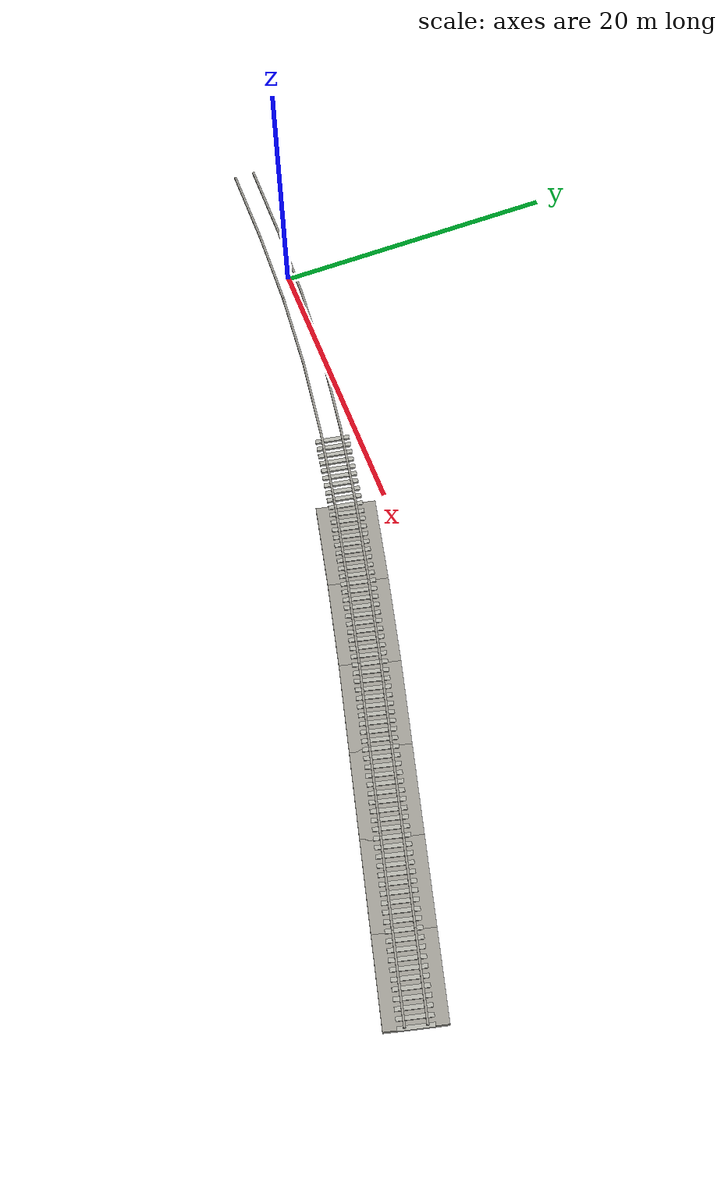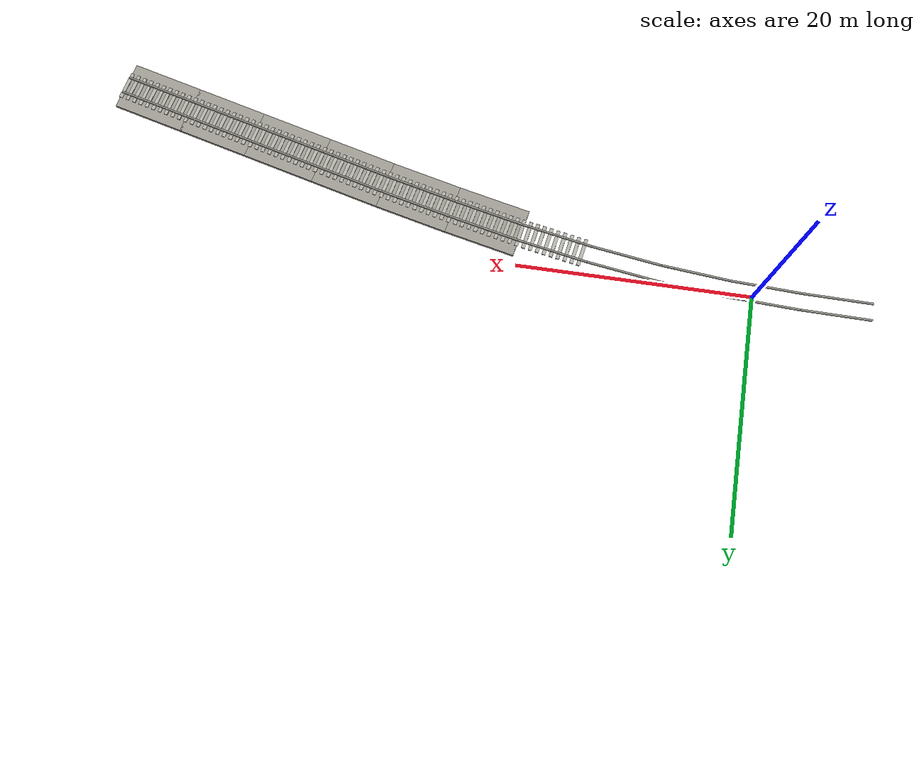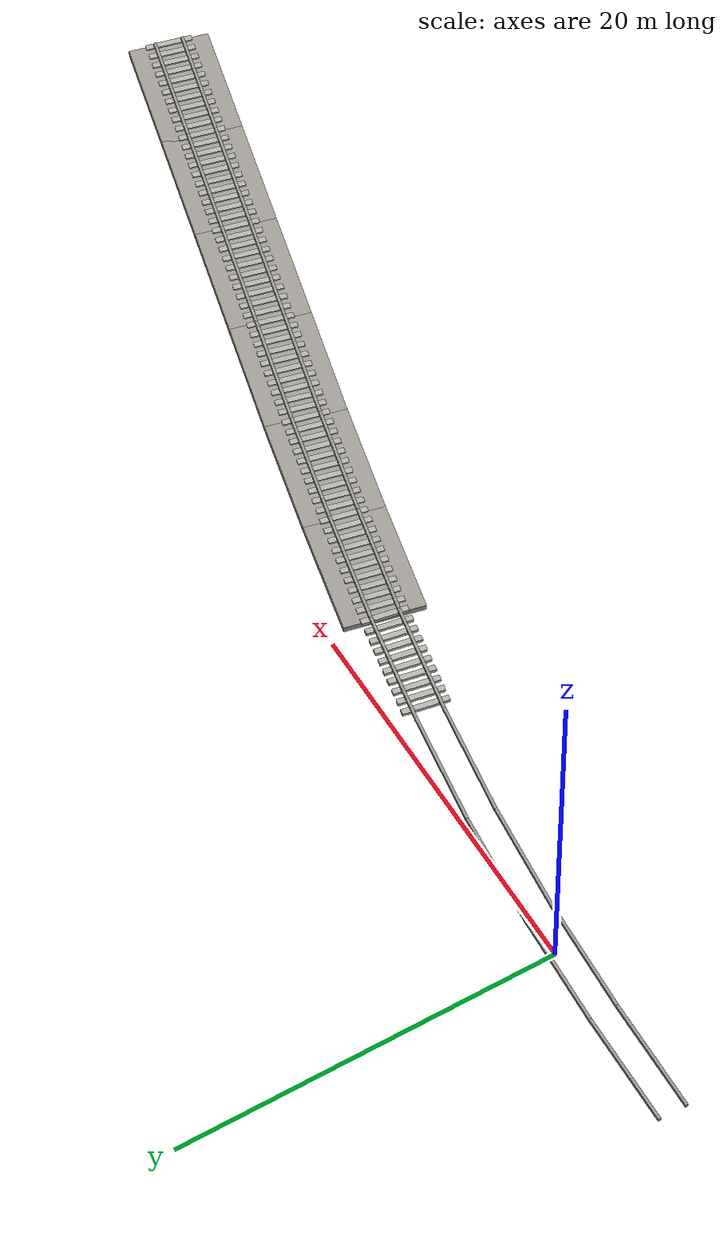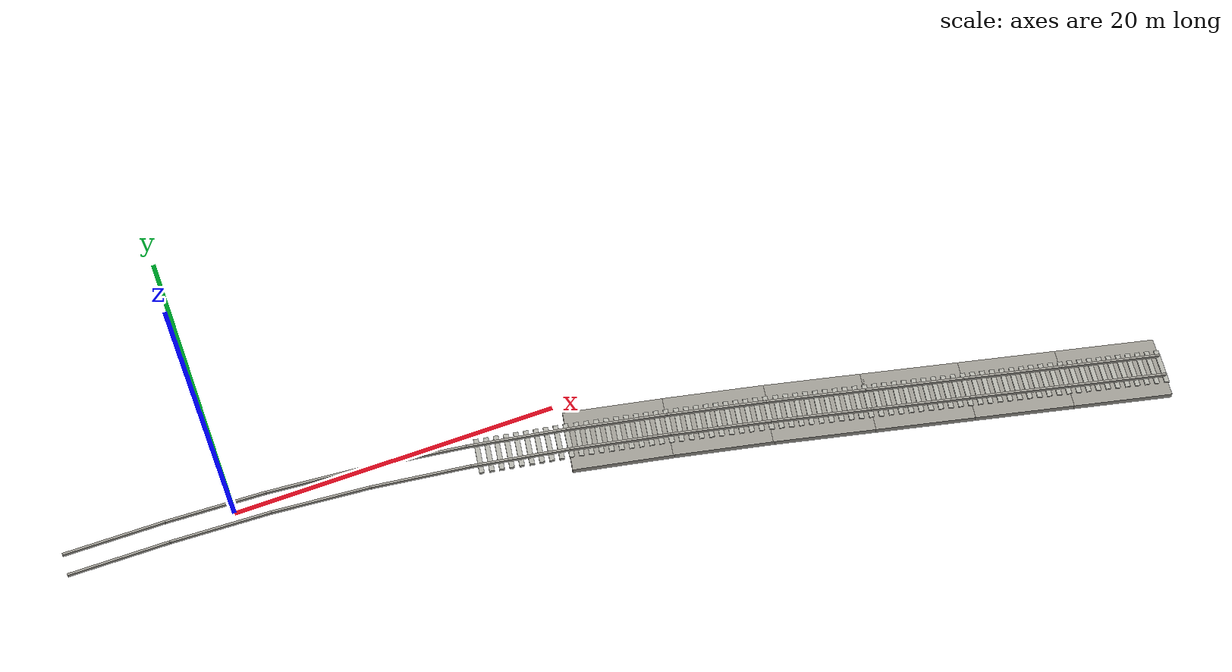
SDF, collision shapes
<?xml version='1.0' encoding='utf-8'?>
<sdf version="1.9">
  <model name="railway_turnout">
    <static>true</static>
    <plugin filename="gz-sim-label-system" name="gz::sim::systems::Label">
      <label>10</label>
    </plugin>
    <link name="turnout_rails_and_ballast">
      <visual name="ballast_transition">
        <geometry>
          <mesh>
            <uri>model://railway_turnout/meshes/ballast_transition.obj</uri>
          </mesh>
        </geometry>
        <material>
          <ambient>0.38 0.38 0.36 1</ambient>
          <diffuse>0.60 0.59 0.56 1</diffuse>
          <pbr>
            <metal>
              <albedo_map>model://track_12m/materials/textures/ballast_albedo.png</albedo_map>
              <roughness>0.98</roughness>
              <metalness>0</metalness>
            </metal>
          </pbr>
        </material>
      </visual>
      <visual name="transition_sleeper_00">
        <pose>-5.700 -0.0390 0.235 0 0 0</pose>
        <geometry>
          <mesh>
            <uri>model://pc_sleeper/meshes/pc_sleeper_concrete.obj</uri>
            <scale>1 1.032465 1</scale>
          </mesh>
        </geometry>
        <material>
          <ambient>0.47 0.47 0.45 1</ambient>
          <diffuse>0.68 0.68 0.65 1</diffuse>
          <pbr>
            <metal>
              <roughness>0.92</roughness>
              <metalness>0</metalness>
            </metal>
          </pbr>
        </material>
      </visual>
      <visual name="transition_sleeper_01">
        <pose>-5.100 -0.0477 0.235 0 0 0</pose>
        <geometry>
          <mesh>
            <uri>model://pc_sleeper/meshes/pc_sleeper_concrete.obj</uri>
            <scale>1 1.039757 1</scale>
          </mesh>
        </geometry>
        <material>
          <ambient>0.47 0.47 0.45 1</ambient>
          <diffuse>0.68 0.68 0.65 1</diffuse>
          <pbr>
            <metal>
              <roughness>0.92</roughness>
              <metalness>0</metalness>
            </metal>
          </pbr>
        </material>
      </visual>
      <visual name="transition_sleeper_02">
        <pose>-4.500 -0.0565 0.235 0 0 0</pose>
        <geometry>
          <mesh>
            <uri>model://pc_sleeper/meshes/pc_sleeper_concrete.obj</uri>
            <scale>1 1.047049 1</scale>
          </mesh>
        </geometry>
        <material>
          <ambient>0.47 0.47 0.45 1</ambient>
          <diffuse>0.68 0.68 0.65 1</diffuse>
          <pbr>
            <metal>
              <roughness>0.92</roughness>
              <metalness>0</metalness>
            </metal>
          </pbr>
        </material>
      </visual>
      <visual name="transition_sleeper_03">
        <pose>-3.900 -0.0652 0.235 0 0 0</pose>
        <geometry>
          <mesh>
            <uri>model://pc_sleeper/meshes/pc_sleeper_concrete.obj</uri>
            <scale>1 1.054340 1</scale>
          </mesh>
        </geometry>
        <material>
          <ambient>0.47 0.47 0.45 1</ambient>
          <diffuse>0.68 0.68 0.65 1</diffuse>
          <pbr>
            <metal>
              <roughness>0.92</roughness>
              <metalness>0</metalness>
            </metal>
          </pbr>
        </material>
      </visual>
      <visual name="transition_sleeper_04">
        <pose>-3.300 -0.0740 0.235 0 0 0</pose>
        <geometry>
          <mesh>
            <uri>model://pc_sleeper/meshes/pc_sleeper_concrete.obj</uri>
            <scale>1 1.061632 1</scale>
          </mesh>
        </geometry>
        <material>
          <ambient>0.47 0.47 0.45 1</ambient>
          <diffuse>0.68 0.68 0.65 1</diffuse>
          <pbr>
            <metal>
              <roughness>0.92</roughness>
              <metalness>0</metalness>
            </metal>
          </pbr>
        </material>
      </visual>
      <visual name="transition_sleeper_05">
        <pose>-2.700 -0.0827 0.235 0 0 0</pose>
        <geometry>
          <mesh>
            <uri>model://pc_sleeper/meshes/pc_sleeper_concrete.obj</uri>
            <scale>1 1.068924 1</scale>
          </mesh>
        </geometry>
        <material>
          <ambient>0.47 0.47 0.45 1</ambient>
          <diffuse>0.68 0.68 0.65 1</diffuse>
          <pbr>
            <metal>
              <roughness>0.92</roughness>
              <metalness>0</metalness>
            </metal>
          </pbr>
        </material>
      </visual>
      <visual name="transition_sleeper_06">
        <pose>-2.100 -0.0915 0.235 0 0 0</pose>
        <geometry>
          <mesh>
            <uri>model://pc_sleeper/meshes/pc_sleeper_concrete.obj</uri>
            <scale>1 1.076215 1</scale>
          </mesh>
        </geometry>
        <material>
          <ambient>0.47 0.47 0.45 1</ambient>
          <diffuse>0.68 0.68 0.65 1</diffuse>
          <pbr>
            <metal>
              <roughness>0.92</roughness>
              <metalness>0</metalness>
            </metal>
          </pbr>
        </material>
      </visual>
      <visual name="transition_sleeper_07">
        <pose>-1.500 -0.1002 0.235 0 0 0</pose>
        <geometry>
          <mesh>
            <uri>model://pc_sleeper/meshes/pc_sleeper_concrete.obj</uri>
            <scale>1 1.083507 1</scale>
          </mesh>
        </geometry>
        <material>
          <ambient>0.47 0.47 0.45 1</ambient>
          <diffuse>0.68 0.68 0.65 1</diffuse>
          <pbr>
            <metal>
              <roughness>0.92</roughness>
              <metalness>0</metalness>
            </metal>
          </pbr>
        </material>
      </visual>
      <visual name="transition_sleeper_08">
        <pose>-0.900 -0.1109 0.235 0 0 0</pose>
        <geometry>
          <mesh>
            <uri>model://pc_sleeper/meshes/pc_sleeper_concrete.obj</uri>
            <scale>1 1.092431 1</scale>
          </mesh>
        </geometry>
        <material>
          <ambient>0.47 0.47 0.45 1</ambient>
          <diffuse>0.68 0.68 0.65 1</diffuse>
          <pbr>
            <metal>
              <roughness>0.92</roughness>
              <metalness>0</metalness>
            </metal>
          </pbr>
        </material>
      </visual>
      <visual name="transition_sleeper_09">
        <pose>-0.300 -0.1314 0.235 0 0 0</pose>
        <geometry>
          <mesh>
            <uri>model://pc_sleeper/meshes/pc_sleeper_concrete.obj</uri>
            <scale>1 1.109514 1</scale>
          </mesh>
        </geometry>
        <material>
          <ambient>0.47 0.47 0.45 1</ambient>
          <diffuse>0.68 0.68 0.65 1</diffuse>
          <pbr>
            <metal>
              <roughness>0.92</roughness>
              <metalness>0</metalness>
            </metal>
          </pbr>
        </material>
      </visual>
      <visual name="transition_sleeper_10">
        <pose>0.300 -0.1519 0.235 0 0 0</pose>
        <geometry>
          <mesh>
            <uri>model://pc_sleeper/meshes/pc_sleeper_concrete.obj</uri>
            <scale>1 1.126597 1</scale>
          </mesh>
        </geometry>
        <material>
          <ambient>0.47 0.47 0.45 1</ambient>
          <diffuse>0.68 0.68 0.65 1</diffuse>
          <pbr>
            <metal>
              <roughness>0.92</roughness>
              <metalness>0</metalness>
            </metal>
          </pbr>
        </material>
      </visual>
      <visual name="transition_sleeper_11">
        <pose>0.900 -0.1724 0.235 0 0 0</pose>
        <geometry>
          <mesh>
            <uri>model://pc_sleeper/meshes/pc_sleeper_concrete.obj</uri>
            <scale>1 1.143681 1</scale>
          </mesh>
        </geometry>
        <material>
          <ambient>0.47 0.47 0.45 1</ambient>
          <diffuse>0.68 0.68 0.65 1</diffuse>
          <pbr>
            <metal>
              <roughness>0.92</roughness>
              <metalness>0</metalness>
            </metal>
          </pbr>
        </material>
      </visual>
      <visual name="transition_sleeper_12">
        <pose>1.500 -0.1929 0.235 0 0 0</pose>
        <geometry>
          <mesh>
            <uri>model://pc_sleeper/meshes/pc_sleeper_concrete.obj</uri>
            <scale>1 1.160764 1</scale>
          </mesh>
        </geometry>
        <material>
          <ambient>0.47 0.47 0.45 1</ambient>
          <diffuse>0.68 0.68 0.65 1</diffuse>
          <pbr>
            <metal>
              <roughness>0.92</roughness>
              <metalness>0</metalness>
            </metal>
          </pbr>
        </material>
      </visual>
      <visual name="transition_sleeper_13">
        <pose>2.100 -0.2134 0.235 0 0 0</pose>
        <geometry>
          <mesh>
            <uri>model://pc_sleeper/meshes/pc_sleeper_concrete.obj</uri>
            <scale>1 1.177847 1</scale>
          </mesh>
        </geometry>
        <material>
          <ambient>0.47 0.47 0.45 1</ambient>
          <diffuse>0.68 0.68 0.65 1</diffuse>
          <pbr>
            <metal>
              <roughness>0.92</roughness>
              <metalness>0</metalness>
            </metal>
          </pbr>
        </material>
      </visual>
      <visual name="transition_sleeper_14">
        <pose>2.700 -0.2339 0.235 0 0 0</pose>
        <geometry>
          <mesh>
            <uri>model://pc_sleeper/meshes/pc_sleeper_concrete.obj</uri>
            <scale>1 1.194931 1</scale>
          </mesh>
        </geometry>
        <material>
          <ambient>0.47 0.47 0.45 1</ambient>
          <diffuse>0.68 0.68 0.65 1</diffuse>
          <pbr>
            <metal>
              <roughness>0.92</roughness>
              <metalness>0</metalness>
            </metal>
          </pbr>
        </material>
      </visual>
      <visual name="transition_sleeper_15">
        <pose>3.300 -0.2544 0.235 0 0 0</pose>
        <geometry>
          <mesh>
            <uri>model://pc_sleeper/meshes/pc_sleeper_concrete.obj</uri>
            <scale>1 1.212014 1</scale>
          </mesh>
        </geometry>
        <material>
          <ambient>0.47 0.47 0.45 1</ambient>
          <diffuse>0.68 0.68 0.65 1</diffuse>
          <pbr>
            <metal>
              <roughness>0.92</roughness>
              <metalness>0</metalness>
            </metal>
          </pbr>
        </material>
      </visual>
      <visual name="transition_sleeper_16">
        <pose>3.900 -0.2749 0.235 0 0 0</pose>
        <geometry>
          <mesh>
            <uri>model://pc_sleeper/meshes/pc_sleeper_concrete.obj</uri>
            <scale>1 1.229097 1</scale>
          </mesh>
        </geometry>
        <material>
          <ambient>0.47 0.47 0.45 1</ambient>
          <diffuse>0.68 0.68 0.65 1</diffuse>
          <pbr>
            <metal>
              <roughness>0.92</roughness>
              <metalness>0</metalness>
            </metal>
          </pbr>
        </material>
      </visual>
      <visual name="transition_sleeper_17">
        <pose>4.500 -0.2954 0.235 0 0 0</pose>
        <geometry>
          <mesh>
            <uri>model://pc_sleeper/meshes/pc_sleeper_concrete.obj</uri>
            <scale>1 1.246181 1</scale>
          </mesh>
        </geometry>
        <material>
          <ambient>0.47 0.47 0.45 1</ambient>
          <diffuse>0.68 0.68 0.65 1</diffuse>
          <pbr>
            <metal>
              <roughness>0.92</roughness>
              <metalness>0</metalness>
            </metal>
          </pbr>
        </material>
      </visual>
      <visual name="transition_sleeper_18">
        <pose>5.100 -0.3183 0.235 0 0 0</pose>
        <geometry>
          <mesh>
            <uri>model://pc_sleeper/meshes/pc_sleeper_concrete.obj</uri>
            <scale>1 1.265278 1</scale>
          </mesh>
        </geometry>
        <material>
          <ambient>0.47 0.47 0.45 1</ambient>
          <diffuse>0.68 0.68 0.65 1</diffuse>
          <pbr>
            <metal>
              <roughness>0.92</roughness>
              <metalness>0</metalness>
            </metal>
          </pbr>
        </material>
      </visual>
      <visual name="transition_sleeper_19">
        <pose>5.700 -0.3533 0.235 0 0 0</pose>
        <geometry>
          <mesh>
            <uri>model://pc_sleeper/meshes/pc_sleeper_concrete.obj</uri>
            <scale>1 1.294444 1</scale>
          </mesh>
        </geometry>
        <material>
          <ambient>0.47 0.47 0.45 1</ambient>
          <diffuse>0.68 0.68 0.65 1</diffuse>
          <pbr>
            <metal>
              <roughness>0.92</roughness>
              <metalness>0</metalness>
            </metal>
          </pbr>
        </material>
      </visual>
      <visual name="transition_sleeper_20">
        <pose>6.300 -0.3883 0.235 0 0 0</pose>
        <geometry>
          <mesh>
            <uri>model://pc_sleeper/meshes/pc_sleeper_concrete.obj</uri>
            <scale>1 1.323611 1</scale>
          </mesh>
        </geometry>
        <material>
          <ambient>0.47 0.47 0.45 1</ambient>
          <diffuse>0.68 0.68 0.65 1</diffuse>
          <pbr>
            <metal>
              <roughness>0.92</roughness>
              <metalness>0</metalness>
            </metal>
          </pbr>
        </material>
      </visual>
      <visual name="transition_sleeper_21">
        <pose>6.900 -0.4233 0.235 0 0 0</pose>
        <geometry>
          <mesh>
            <uri>model://pc_sleeper/meshes/pc_sleeper_concrete.obj</uri>
            <scale>1 1.352778 1</scale>
          </mesh>
        </geometry>
        <material>
          <ambient>0.47 0.47 0.45 1</ambient>
          <diffuse>0.68 0.68 0.65 1</diffuse>
          <pbr>
            <metal>
              <roughness>0.92</roughness>
              <metalness>0</metalness>
            </metal>
          </pbr>
        </material>
      </visual>
      <visual name="transition_sleeper_22">
        <pose>7.500 -0.4583 0.235 0 0 0</pose>
        <geometry>
          <mesh>
            <uri>model://pc_sleeper/meshes/pc_sleeper_concrete.obj</uri>
            <scale>1 1.381944 1</scale>
          </mesh>
        </geometry>
        <material>
          <ambient>0.47 0.47 0.45 1</ambient>
          <diffuse>0.68 0.68 0.65 1</diffuse>
          <pbr>
            <metal>
              <roughness>0.92</roughness>
              <metalness>0</metalness>
            </metal>
          </pbr>
        </material>
      </visual>
      <visual name="transition_sleeper_23">
        <pose>8.100 -0.4933 0.235 0 0 0</pose>
        <geometry>
          <mesh>
            <uri>model://pc_sleeper/meshes/pc_sleeper_concrete.obj</uri>
            <scale>1 1.411111 1</scale>
          </mesh>
        </geometry>
        <material>
          <ambient>0.47 0.47 0.45 1</ambient>
          <diffuse>0.68 0.68 0.65 1</diffuse>
          <pbr>
            <metal>
              <roughness>0.92</roughness>
              <metalness>0</metalness>
            </metal>
          </pbr>
        </material>
      </visual>
      <visual name="transition_sleeper_24">
        <pose>8.700 -0.5283 0.235 0 0 0</pose>
        <geometry>
          <mesh>
            <uri>model://pc_sleeper/meshes/pc_sleeper_concrete.obj</uri>
            <scale>1 1.440278 1</scale>
          </mesh>
        </geometry>
        <material>
          <ambient>0.47 0.47 0.45 1</ambient>
          <diffuse>0.68 0.68 0.65 1</diffuse>
          <pbr>
            <metal>
              <roughness>0.92</roughness>
              <metalness>0</metalness>
            </metal>
          </pbr>
        </material>
      </visual>
      <visual name="transition_sleeper_25">
        <pose>9.300 -0.5633 0.235 0 0 0</pose>
        <geometry>
          <mesh>
            <uri>model://pc_sleeper/meshes/pc_sleeper_concrete.obj</uri>
            <scale>1 1.469444 1</scale>
          </mesh>
        </geometry>
        <material>
          <ambient>0.47 0.47 0.45 1</ambient>
          <diffuse>0.68 0.68 0.65 1</diffuse>
          <pbr>
            <metal>
              <roughness>0.92</roughness>
              <metalness>0</metalness>
            </metal>
          </pbr>
        </material>
      </visual>
      <visual name="transition_sleeper_26">
        <pose>9.900 -0.5983 0.235 0 0 0</pose>
        <geometry>
          <mesh>
            <uri>model://pc_sleeper/meshes/pc_sleeper_concrete.obj</uri>
            <scale>1 1.498611 1</scale>
          </mesh>
        </geometry>
        <material>
          <ambient>0.47 0.47 0.45 1</ambient>
          <diffuse>0.68 0.68 0.65 1</diffuse>
          <pbr>
            <metal>
              <roughness>0.92</roughness>
              <metalness>0</metalness>
            </metal>
          </pbr>
        </material>
      </visual>
      <visual name="transition_sleeper_27">
        <pose>10.500 -0.6333 0.235 0 0 0</pose>
        <geometry>
          <mesh>
            <uri>model://pc_sleeper/meshes/pc_sleeper_concrete.obj</uri>
            <scale>1 1.527778 1</scale>
          </mesh>
        </geometry>
        <material>
          <ambient>0.47 0.47 0.45 1</ambient>
          <diffuse>0.68 0.68 0.65 1</diffuse>
          <pbr>
            <metal>
              <roughness>0.92</roughness>
              <metalness>0</metalness>
            </metal>
          </pbr>
        </material>
      </visual>
      <visual name="transition_sleeper_28">
        <pose>11.100 -0.6706 0.235 0 0 0</pose>
        <geometry>
          <mesh>
            <uri>model://pc_sleeper/meshes/pc_sleeper_concrete.obj</uri>
            <scale>1 1.558854 1</scale>
          </mesh>
        </geometry>
        <material>
          <ambient>0.47 0.47 0.45 1</ambient>
          <diffuse>0.68 0.68 0.65 1</diffuse>
          <pbr>
            <metal>
              <roughness>0.92</roughness>
              <metalness>0</metalness>
            </metal>
          </pbr>
        </material>
      </visual>
      <visual name="transition_sleeper_29">
        <pose>11.700 -0.7194 0.235 0 0 0</pose>
        <geometry>
          <mesh>
            <uri>model://pc_sleeper/meshes/pc_sleeper_concrete.obj</uri>
            <scale>1 1.599479 1</scale>
          </mesh>
        </geometry>
        <material>
          <ambient>0.47 0.47 0.45 1</ambient>
          <diffuse>0.68 0.68 0.65 1</diffuse>
          <pbr>
            <metal>
              <roughness>0.92</roughness>
              <metalness>0</metalness>
            </metal>
          </pbr>
        </material>
      </visual>
      <visual name="transition_sleeper_30">
        <pose>12.300 -0.7681 0.235 0 0 0</pose>
        <geometry>
          <mesh>
            <uri>model://pc_sleeper/meshes/pc_sleeper_concrete.obj</uri>
            <scale>1 1.640104 1</scale>
          </mesh>
        </geometry>
        <material>
          <ambient>0.47 0.47 0.45 1</ambient>
          <diffuse>0.68 0.68 0.65 1</diffuse>
          <pbr>
            <metal>
              <roughness>0.92</roughness>
              <metalness>0</metalness>
            </metal>
          </pbr>
        </material>
      </visual>
      <visual name="transition_sleeper_31">
        <pose>12.900 -0.8169 0.235 0 0 0</pose>
        <geometry>
          <mesh>
            <uri>model://pc_sleeper/meshes/pc_sleeper_concrete.obj</uri>
            <scale>1 1.680729 1</scale>
          </mesh>
        </geometry>
        <material>
          <ambient>0.47 0.47 0.45 1</ambient>
          <diffuse>0.68 0.68 0.65 1</diffuse>
          <pbr>
            <metal>
              <roughness>0.92</roughness>
              <metalness>0</metalness>
            </metal>
          </pbr>
        </material>
      </visual>
      <visual name="transition_sleeper_32">
        <pose>13.500 -0.8656 0.235 0 0 0</pose>
        <geometry>
          <mesh>
            <uri>model://pc_sleeper/meshes/pc_sleeper_concrete.obj</uri>
            <scale>1 1.721354 1</scale>
          </mesh>
        </geometry>
        <material>
          <ambient>0.47 0.47 0.45 1</ambient>
          <diffuse>0.68 0.68 0.65 1</diffuse>
          <pbr>
            <metal>
              <roughness>0.92</roughness>
              <metalness>0</metalness>
            </metal>
          </pbr>
        </material>
      </visual>
      <visual name="transition_sleeper_33">
        <pose>14.100 -0.9144 0.235 0 0 0</pose>
        <geometry>
          <mesh>
            <uri>model://pc_sleeper/meshes/pc_sleeper_concrete.obj</uri>
            <scale>1 1.761979 1</scale>
          </mesh>
        </geometry>
        <material>
          <ambient>0.47 0.47 0.45 1</ambient>
          <diffuse>0.68 0.68 0.65 1</diffuse>
          <pbr>
            <metal>
              <roughness>0.92</roughness>
              <metalness>0</metalness>
            </metal>
          </pbr>
        </material>
      </visual>
      <collision name="rail_l_collision_0">
        <pose>-6.9904 0.6774 0.516 0 0 -0.013333</pose>
        <geometry>
          <box>
            <size>6.0505 0.145 0.192</size>
          </box>
        </geometry>
      </collision>
      <collision name="rail_r_collision_0">
        <pose>-7.009566 -0.757436 0.516000 0.000000 0.000000 -0.013333</pose>
        <geometry>
          <box>
            <size>6.0505 0.145 0.192</size>
          </box>
        </geometry>
      </collision>
      <collision name="rail_l_collision_1">
        <pose>-0.9677 0.5018 0.516 0 0 -0.044970</pose>
        <geometry>
          <box>
            <size>6.0561 0.145 0.192</size>
          </box>
        </geometry>
      </collision>
      <collision name="rail_r_collision_1">
        <pose>-1.032255 -0.931775 0.516000 0.000000 0.000000 -0.044970</pose>
        <geometry>
          <box>
            <size>6.0561 0.145 0.192</size>
          </box>
        </geometry>
      </collision>
      <collision name="rail_l_collision_2">
        <pose>5.0655 0.0895 0.516 0 0 -0.091411</pose>
        <geometry>
          <box>
            <size>6.0752 0.145 0.192</size>
          </box>
        </geometry>
      </collision>
      <collision name="rail_r_collision_2">
        <pose>4.934504 -1.339504 0.516000 0.000000 0.000000 -0.091411</pose>
        <geometry>
          <box>
            <size>6.0752 0.145 0.192</size>
          </box>
        </geometry>
      </collision>
      <collision name="rail_l_collision_3">
        <pose>11.1006 -0.6146 0.516 0 0 -0.140730</pose>
        <geometry>
          <box>
            <size>6.1099 0.145 0.192</size>
          </box>
        </geometry>
      </collision>
      <collision name="rail_r_collision_3">
        <pose>10.899359 -2.035407 0.516000 0.000000 0.000000 -0.140730</pose>
        <geometry>
          <box>
            <size>6.1099 0.145 0.192</size>
          </box>
        </geometry>
      </collision>
      <collision name="rail_l_collision_4">
        <pose>17.1294 -1.5943 0.516 0 0 -0.181320</pose>
        <geometry>
          <box>
            <size>6.1500 0.145 0.192</size>
          </box>
        </geometry>
      </collision>
      <collision name="rail_r_collision_4">
        <pose>16.870615 -3.005738 0.516000 0.000000 0.000000 -0.181320</pose>
        <geometry>
          <box>
            <size>6.1500 0.145 0.192</size>
          </box>
        </geometry>
      </collision>
      <collision name="ballast_collision_5">
        <pose>23.0000 -3.5000 0.17 0 0 -0.213369</pose>
        <geometry>
          <box>
            <size>6.2892 4.15 0.34</size>
          </box>
        </geometry>
      </collision>
      <visual name="ballast_5">
        <pose>23.000000 -3.500000 0.000000 0.000000 0.000000 -0.213369</pose>
        <geometry>
          <mesh>
            <uri>model://track_12m/meshes/ballast_bed.obj</uri>
            <scale>0.5266000 1 1</scale>
          </mesh>
        </geometry>
        <material>
          <diffuse>0.60 0.59 0.56 1</diffuse>
          <pbr>
            <metal>
              <albedo_map>model://track_12m/materials/textures/ballast_albedo.png</albedo_map>
              <roughness>0.98</roughness>
              <metalness>0</metalness>
            </metal>
          </pbr>
          <ambient>0.38 0.38 0.36 1</ambient>
        </material>
      </visual>
      <collision name="rail_l_collision_5">
        <pose>23.1519 -2.7988 0.516 0 0 -0.213369</pose>
        <geometry>
          <box>
            <size>6.1892 0.145 0.192</size>
          </box>
        </geometry>
      </collision>
      <collision name="rail_r_collision_5">
        <pose>22.848067 -4.201229 0.516000 0.000000 0.000000 -0.213369</pose>
        <geometry>
          <box>
            <size>6.1892 0.145 0.192</size>
          </box>
        </geometry>
      </collision>
      <collision name="ballast_collision_6">
        <pose>29.0000 -4.8500 0.17 0 0 -0.229232</pose>
        <geometry>
          <box>
            <size>6.3112 4.15 0.34</size>
          </box>
        </geometry>
      </collision>
      <visual name="ballast_6">
        <pose>29.000000 -4.850000 0.000000 0.000000 0.000000 -0.229232</pose>
        <geometry>
          <mesh>
            <uri>model://track_12m/meshes/ballast_bed.obj</uri>
            <scale>0.5284333 1 1</scale>
          </mesh>
        </geometry>
        <material>
          <diffuse>0.60 0.59 0.56 1</diffuse>
          <pbr>
            <metal>
              <albedo_map>model://track_12m/materials/textures/ballast_albedo.png</albedo_map>
              <roughness>0.98</roughness>
              <metalness>0</metalness>
            </metal>
          </pbr>
          <ambient>0.38 0.38 0.36 1</ambient>
        </material>
      </visual>
      <collision name="rail_l_collision_6">
        <pose>29.1630 -4.1513 0.516 0 0 -0.229232</pose>
        <geometry>
          <box>
            <size>6.2112 0.145 0.192</size>
          </box>
        </geometry>
      </collision>
      <collision name="rail_r_collision_6">
        <pose>28.836963 -5.548731 0.516000 0.000000 0.000000 -0.229232</pose>
        <geometry>
          <box>
            <size>6.2112 0.145 0.192</size>
          </box>
        </geometry>
      </collision>
      <collision name="ballast_collision_7">
        <pose>35.0000 -6.3000 0.17 0 0 -0.244979</pose>
        <geometry>
          <box>
            <size>6.3347 4.15 0.34</size>
          </box>
        </geometry>
      </collision>
      <visual name="ballast_7">
        <pose>35.000000 -6.300000 0.000000 0.000000 0.000000 -0.244979</pose>
        <geometry>
          <mesh>
            <uri>model://track_12m/meshes/ballast_bed.obj</uri>
            <scale>0.5303917 1 1</scale>
          </mesh>
        </geometry>
        <material>
          <diffuse>0.60 0.59 0.56 1</diffuse>
          <pbr>
            <metal>
              <albedo_map>model://track_12m/materials/textures/ballast_albedo.png</albedo_map>
              <roughness>0.98</roughness>
              <metalness>0</metalness>
            </metal>
          </pbr>
          <ambient>0.38 0.38 0.36 1</ambient>
        </material>
      </visual>
      <collision name="rail_l_collision_7">
        <pose>35.1740 -5.6039 0.516 0 0 -0.244979</pose>
        <geometry>
          <box>
            <size>6.2347 0.145 0.192</size>
          </box>
        </geometry>
      </collision>
      <collision name="rail_r_collision_7">
        <pose>34.825980 -6.996077 0.516000 0.000000 0.000000 -0.244979</pose>
        <geometry>
          <box>
            <size>6.2347 0.145 0.192</size>
          </box>
        </geometry>
      </collision>
      <collision name="ballast_collision_8">
        <pose>41.0000 -7.8000 0.17 0 0 -0.244979</pose>
        <geometry>
          <box>
            <size>6.3347 4.15 0.34</size>
          </box>
        </geometry>
      </collision>
      <visual name="ballast_8">
        <pose>41.000000 -7.800000 0.000000 0.000000 0.000000 -0.244979</pose>
        <geometry>
          <mesh>
            <uri>model://track_12m/meshes/ballast_bed.obj</uri>
            <scale>0.5303917 1 1</scale>
          </mesh>
        </geometry>
        <material>
          <diffuse>0.60 0.59 0.56 1</diffuse>
          <pbr>
            <metal>
              <albedo_map>model://track_12m/materials/textures/ballast_albedo.png</albedo_map>
              <roughness>0.98</roughness>
              <metalness>0</metalness>
            </metal>
          </pbr>
          <ambient>0.38 0.38 0.36 1</ambient>
        </material>
      </visual>
      <collision name="rail_l_collision_8">
        <pose>41.1740 -7.1039 0.516 0 0 -0.244979</pose>
        <geometry>
          <box>
            <size>6.2347 0.145 0.192</size>
          </box>
        </geometry>
      </collision>
      <collision name="rail_r_collision_8">
        <pose>40.825980 -8.496077 0.516000 0.000000 0.000000 -0.244979</pose>
        <geometry>
          <box>
            <size>6.2347 0.145 0.192</size>
          </box>
        </geometry>
      </collision>
      <collision name="ballast_collision_9">
        <pose>47.0000 -9.3000 0.17 0 0 -0.244979</pose>
        <geometry>
          <box>
            <size>6.3347 4.15 0.34</size>
          </box>
        </geometry>
      </collision>
      <visual name="ballast_9">
        <pose>47.000000 -9.300000 0.000000 0.000000 0.000000 -0.244979</pose>
        <geometry>
          <mesh>
            <uri>model://track_12m/meshes/ballast_bed.obj</uri>
            <scale>0.5303917 1 1</scale>
          </mesh>
        </geometry>
        <material>
          <diffuse>0.60 0.59 0.56 1</diffuse>
          <pbr>
            <metal>
              <albedo_map>model://track_12m/materials/textures/ballast_albedo.png</albedo_map>
              <roughness>0.98</roughness>
              <metalness>0</metalness>
            </metal>
          </pbr>
          <ambient>0.38 0.38 0.36 1</ambient>
        </material>
      </visual>
      <collision name="rail_l_collision_9">
        <pose>47.1740 -8.6039 0.516 0 0 -0.244979</pose>
        <geometry>
          <box>
            <size>6.2347 0.145 0.192</size>
          </box>
        </geometry>
      </collision>
      <collision name="rail_r_collision_9">
        <pose>46.825980 -9.996077 0.516000 0.000000 0.000000 -0.244979</pose>
        <geometry>
          <box>
            <size>6.2347 0.145 0.192</size>
          </box>
        </geometry>
      </collision>
      <collision name="ballast_collision_10">
        <pose>53.0000 -10.8000 0.17 0 0 -0.244979</pose>
        <geometry>
          <box>
            <size>6.3347 4.15 0.34</size>
          </box>
        </geometry>
      </collision>
      <visual name="ballast_10">
        <pose>53.000000 -10.800000 0.000000 0.000000 0.000000 -0.244979</pose>
        <geometry>
          <mesh>
            <uri>model://track_12m/meshes/ballast_bed.obj</uri>
            <scale>0.5303917 1 1</scale>
          </mesh>
        </geometry>
        <material>
          <diffuse>0.60 0.59 0.56 1</diffuse>
          <pbr>
            <metal>
              <albedo_map>model://track_12m/materials/textures/ballast_albedo.png</albedo_map>
              <roughness>0.98</roughness>
              <metalness>0</metalness>
            </metal>
          </pbr>
          <ambient>0.38 0.38 0.36 1</ambient>
        </material>
      </visual>
      <collision name="rail_l_collision_10">
        <pose>53.1740 -10.1039 0.516 0 0 -0.244979</pose>
        <geometry>
          <box>
            <size>6.2347 0.145 0.192</size>
          </box>
        </geometry>
      </collision>
      <collision name="rail_r_collision_10">
        <pose>52.825980 -11.496077 0.516000 0.000000 0.000000 -0.244979</pose>
        <geometry>
          <box>
            <size>6.2347 0.145 0.192</size>
          </box>
        </geometry>
      </collision>
      <!-- Moving point blades and check rails make the switch readable in close-range RGB and masks. -->
      <visual name="point_blade_inner">
        <pose>-4.0 -0.19 0.588 0 0 -0.025</pose>
        <geometry>
          <box>
            <size>11.8 0.045 0.048</size>
          </box>
        </geometry>
        <material>
          <ambient>0.13 0.09 0.065 1</ambient>
          <diffuse>0.31 0.22 0.16 1</diffuse>
          <specular>0.72 0.72 0.72 1</specular>
          <pbr>
            <metal>
              <roughness>0.48</roughness>
              <metalness>0.72</metalness>
            </metal>
          </pbr>
        </material>
      </visual>
      <visual name="check_rail_main">
        <pose>8.0 0.49 0.588 0 0 0</pose>
        <geometry>
          <box>
            <size>7.0 0.055 0.050</size>
          </box>
        </geometry>
        <material>
          <ambient>0.13 0.09 0.065 1</ambient>
          <diffuse>0.31 0.22 0.16 1</diffuse>
          <specular>0.72 0.72 0.72 1</specular>
          <pbr>
            <metal>
              <roughness>0.48</roughness>
              <metalness>0.72</metalness>
            </metal>
          </pbr>
        </material>
      </visual>
      <visual name="check_rail_branch">
        <pose>8.1 -1.41 0.588 0 0 -0.12</pose>
        <geometry>
          <box>
            <size>7.0 0.055 0.050</size>
          </box>
        </geometry>
        <material>
          <ambient>0.13 0.09 0.065 1</ambient>
          <diffuse>0.31 0.22 0.16 1</diffuse>
          <specular>0.72 0.72 0.72 1</specular>
          <pbr>
            <metal>
              <roughness>0.48</roughness>
              <metalness>0.72</metalness>
            </metal>
          </pbr>
        </material>
      </visual>
      <visual name="switch_motor">
        <pose>-5.0 2.10 0.56 0 0 0</pose>
        <geometry>
          <box>
            <size>1.15 0.72 0.45</size>
          </box>
        </geometry>
        <material>
          <diffuse>0.18 0.22 0.20 1</diffuse>
          <pbr>
            <metal>
              <roughness>0.54</roughness>
              <metalness>0.48</metalness>
            </metal>
          </pbr>
        </material>
      </visual>
      <visual name="switch_rod">
        <pose>-4.2 1.20 0.48 0 0 -0.25</pose>
        <geometry>
          <box>
            <size>2.10 0.07 0.07</size>
          </box>
        </geometry>
        <material>
          <diffuse>0.36 0.37 0.35 1</diffuse>
        </material>
      </visual>
      <visual name="buffer_beam">
        <pose>56.5 -11.68 0.92 0 0 -0.245</pose>
        <geometry>
          <box>
            <size>0.24 2.45 0.22</size>
          </box>
        </geometry>
        <material>
          <diffuse>0.88 0.72 0.08 1</diffuse>
        </material>
      </visual>
      <visual name="buffer_post_l">
        <pose>56.2 -10.85 0.63 0 0 -0.245</pose>
        <geometry>
          <box>
            <size>0.20 0.20 0.92</size>
          </box>
        </geometry>
        <material>
          <diffuse>0.24 0.25 0.24 1</diffuse>
        </material>
      </visual>
      <visual name="buffer_post_r">
        <pose>56.7 -12.48 0.63 0 0 -0.245</pose>
        <geometry>
          <box>
            <size>0.20 0.20 0.92</size>
          </box>
        </geometry>
        <material>
          <diffuse>0.24 0.25 0.24 1</diffuse>
        </material>
      </visual>
      <visual name="branch_rail_left_0">
        <pose>-6.990400 0.677400 0.459 0 0 -0.013333</pose>
        <geometry>
          <mesh>
            <uri>model://track_12m/meshes/rail_profile_12m.obj</uri>
            <scale>0.5067083 1 1</scale>
          </mesh>
        </geometry>
        <material>
          <ambient>0.13 0.09 0.065 1</ambient>
          <diffuse>0.31 0.22 0.16 1</diffuse>
          <specular>0.30 0.25 0.20 1</specular>
          <pbr>
            <metal>
              <roughness>0.48</roughness>
              <metalness>0.72</metalness>
            </metal>
          </pbr>
        </material>
      </visual>
      <visual name="branch_rail_right_0">
        <pose>-7.009532 -0.757472 0.459 0 0 -0.013333</pose>
        <geometry>
          <mesh>
            <uri>model://track_12m/meshes/rail_profile_12m.obj</uri>
            <scale>0.5067083 1 1</scale>
          </mesh>
        </geometry>
        <material>
          <ambient>0.13 0.09 0.065 1</ambient>
          <diffuse>0.31 0.22 0.16 1</diffuse>
          <specular>0.30 0.25 0.20 1</specular>
          <pbr>
            <metal>
              <roughness>0.48</roughness>
              <metalness>0.72</metalness>
            </metal>
          </pbr>
        </material>
      </visual>
      <visual name="branch_rail_left_1">
        <pose>-0.967700 0.501800 0.459 0 0 -0.044970</pose>
        <geometry>
          <mesh>
            <uri>model://track_12m/meshes/rail_profile_12m.obj</uri>
            <scale>0.5071750 1 1</scale>
          </mesh>
        </geometry>
        <material>
          <ambient>0.13 0.09 0.065 1</ambient>
          <diffuse>0.31 0.22 0.16 1</diffuse>
          <specular>0.30 0.25 0.20 1</specular>
          <pbr>
            <metal>
              <roughness>0.48</roughness>
              <metalness>0.72</metalness>
            </metal>
          </pbr>
        </material>
      </visual>
      <visual name="branch_rail_right_1">
        <pose>-1.032210 -0.931749 0.459 0 0 -0.044970</pose>
        <geometry>
          <mesh>
            <uri>model://track_12m/meshes/rail_profile_12m.obj</uri>
            <scale>0.5071750 1 1</scale>
          </mesh>
        </geometry>
        <material>
          <ambient>0.13 0.09 0.065 1</ambient>
          <diffuse>0.31 0.22 0.16 1</diffuse>
          <specular>0.30 0.25 0.20 1</specular>
          <pbr>
            <metal>
              <roughness>0.48</roughness>
              <metalness>0.72</metalness>
            </metal>
          </pbr>
        </material>
      </visual>
      <visual name="branch_rail_left_2">
        <pose>5.065500 0.089500 0.459 0 0 -0.091411</pose>
        <geometry>
          <mesh>
            <uri>model://track_12m/meshes/rail_profile_12m.obj</uri>
            <scale>0.5087667 1 1</scale>
          </mesh>
        </geometry>
        <material>
          <ambient>0.13 0.09 0.065 1</ambient>
          <diffuse>0.31 0.22 0.16 1</diffuse>
          <specular>0.30 0.25 0.20 1</specular>
          <pbr>
            <metal>
              <roughness>0.48</roughness>
              <metalness>0.72</metalness>
            </metal>
          </pbr>
        </material>
      </visual>
      <visual name="branch_rail_right_2">
        <pose>4.934508 -1.339509 0.459 0 0 -0.091411</pose>
        <geometry>
          <mesh>
            <uri>model://track_12m/meshes/rail_profile_12m.obj</uri>
            <scale>0.5087667 1 1</scale>
          </mesh>
        </geometry>
        <material>
          <ambient>0.13 0.09 0.065 1</ambient>
          <diffuse>0.31 0.22 0.16 1</diffuse>
          <specular>0.30 0.25 0.20 1</specular>
          <pbr>
            <metal>
              <roughness>0.48</roughness>
              <metalness>0.72</metalness>
            </metal>
          </pbr>
        </material>
      </visual>
      <visual name="branch_rail_left_3">
        <pose>11.100600 -0.614600 0.459 0 0 -0.140730</pose>
        <geometry>
          <mesh>
            <uri>model://track_12m/meshes/rail_profile_12m.obj</uri>
            <scale>0.5116583 1 1</scale>
          </mesh>
        </geometry>
        <material>
          <ambient>0.13 0.09 0.065 1</ambient>
          <diffuse>0.31 0.22 0.16 1</diffuse>
          <specular>0.30 0.25 0.20 1</specular>
          <pbr>
            <metal>
              <roughness>0.48</roughness>
              <metalness>0.72</metalness>
            </metal>
          </pbr>
        </material>
      </visual>
      <visual name="branch_rail_right_3">
        <pose>10.899318 -2.035413 0.459 0 0 -0.140730</pose>
        <geometry>
          <mesh>
            <uri>model://track_12m/meshes/rail_profile_12m.obj</uri>
            <scale>0.5116583 1 1</scale>
          </mesh>
        </geometry>
        <material>
          <ambient>0.13 0.09 0.065 1</ambient>
          <diffuse>0.31 0.22 0.16 1</diffuse>
          <specular>0.30 0.25 0.20 1</specular>
          <pbr>
            <metal>
              <roughness>0.48</roughness>
              <metalness>0.72</metalness>
            </metal>
          </pbr>
        </material>
      </visual>
      <visual name="branch_rail_left_4">
        <pose>17.129400 -1.594300 0.459 0 0 -0.181320</pose>
        <geometry>
          <mesh>
            <uri>model://track_12m/meshes/rail_profile_12m.obj</uri>
            <scale>0.5150000 1 1</scale>
          </mesh>
        </geometry>
        <material>
          <ambient>0.13 0.09 0.065 1</ambient>
          <diffuse>0.31 0.22 0.16 1</diffuse>
          <specular>0.30 0.25 0.20 1</specular>
          <pbr>
            <metal>
              <roughness>0.48</roughness>
              <metalness>0.72</metalness>
            </metal>
          </pbr>
        </material>
      </visual>
      <visual name="branch_rail_right_4">
        <pose>16.870629 -3.005775 0.459 0 0 -0.181320</pose>
        <geometry>
          <mesh>
            <uri>model://track_12m/meshes/rail_profile_12m.obj</uri>
            <scale>0.5150000 1 1</scale>
          </mesh>
        </geometry>
        <material>
          <ambient>0.13 0.09 0.065 1</ambient>
          <diffuse>0.31 0.22 0.16 1</diffuse>
          <specular>0.30 0.25 0.20 1</specular>
          <pbr>
            <metal>
              <roughness>0.48</roughness>
              <metalness>0.72</metalness>
            </metal>
          </pbr>
        </material>
      </visual>
      <visual name="branch_rail_left_5">
        <pose>23.151900 -2.798800 0.459 0 0 -0.213369</pose>
        <geometry>
          <mesh>
            <uri>model://track_12m/meshes/rail_profile_12m.obj</uri>
            <scale>0.5182667 1 1</scale>
          </mesh>
        </geometry>
        <material>
          <ambient>0.13 0.09 0.065 1</ambient>
          <diffuse>0.31 0.22 0.16 1</diffuse>
          <specular>0.30 0.25 0.20 1</specular>
          <pbr>
            <metal>
              <roughness>0.48</roughness>
              <metalness>0.72</metalness>
            </metal>
          </pbr>
        </material>
      </visual>
      <visual name="branch_rail_right_5">
        <pose>22.848033 -4.201259 0.459 0 0 -0.213369</pose>
        <geometry>
          <mesh>
            <uri>model://track_12m/meshes/rail_profile_12m.obj</uri>
            <scale>0.5182667 1 1</scale>
          </mesh>
        </geometry>
        <material>
          <ambient>0.13 0.09 0.065 1</ambient>
          <diffuse>0.31 0.22 0.16 1</diffuse>
          <specular>0.30 0.25 0.20 1</specular>
          <pbr>
            <metal>
              <roughness>0.48</roughness>
              <metalness>0.72</metalness>
            </metal>
          </pbr>
        </material>
      </visual>
      <visual name="branch_rail_left_6">
        <pose>29.163000 -4.151300 0.459 0 0 -0.229232</pose>
        <geometry>
          <mesh>
            <uri>model://track_12m/meshes/rail_profile_12m.obj</uri>
            <scale>0.5201000 1 1</scale>
          </mesh>
        </geometry>
        <material>
          <ambient>0.13 0.09 0.065 1</ambient>
          <diffuse>0.31 0.22 0.16 1</diffuse>
          <specular>0.30 0.25 0.20 1</specular>
          <pbr>
            <metal>
              <roughness>0.48</roughness>
              <metalness>0.72</metalness>
            </metal>
          </pbr>
        </material>
      </visual>
      <visual name="branch_rail_right_6">
        <pose>28.836925 -5.548762 0.459 0 0 -0.229232</pose>
        <geometry>
          <mesh>
            <uri>model://track_12m/meshes/rail_profile_12m.obj</uri>
            <scale>0.5201000 1 1</scale>
          </mesh>
        </geometry>
        <material>
          <ambient>0.13 0.09 0.065 1</ambient>
          <diffuse>0.31 0.22 0.16 1</diffuse>
          <specular>0.30 0.25 0.20 1</specular>
          <pbr>
            <metal>
              <roughness>0.48</roughness>
              <metalness>0.72</metalness>
            </metal>
          </pbr>
        </material>
      </visual>
      <visual name="branch_rail_left_7">
        <pose>35.174000 -5.603900 0.459 0 0 -0.244979</pose>
        <geometry>
          <mesh>
            <uri>model://track_12m/meshes/rail_profile_12m.obj</uri>
            <scale>0.5220583 1 1</scale>
          </mesh>
        </geometry>
        <material>
          <ambient>0.13 0.09 0.065 1</ambient>
          <diffuse>0.31 0.22 0.16 1</diffuse>
          <specular>0.30 0.25 0.20 1</specular>
          <pbr>
            <metal>
              <roughness>0.48</roughness>
              <metalness>0.72</metalness>
            </metal>
          </pbr>
        </material>
      </visual>
      <visual name="branch_rail_right_7">
        <pose>34.825961 -6.996054 0.459 0 0 -0.244979</pose>
        <geometry>
          <mesh>
            <uri>model://track_12m/meshes/rail_profile_12m.obj</uri>
            <scale>0.5220583 1 1</scale>
          </mesh>
        </geometry>
        <material>
          <ambient>0.13 0.09 0.065 1</ambient>
          <diffuse>0.31 0.22 0.16 1</diffuse>
          <specular>0.30 0.25 0.20 1</specular>
          <pbr>
            <metal>
              <roughness>0.48</roughness>
              <metalness>0.72</metalness>
            </metal>
          </pbr>
        </material>
      </visual>
      <visual name="branch_rail_left_8">
        <pose>41.174000 -7.103900 0.459 0 0 -0.244979</pose>
        <geometry>
          <mesh>
            <uri>model://track_12m/meshes/rail_profile_12m.obj</uri>
            <scale>0.5220583 1 1</scale>
          </mesh>
        </geometry>
        <material>
          <ambient>0.13 0.09 0.065 1</ambient>
          <diffuse>0.31 0.22 0.16 1</diffuse>
          <specular>0.30 0.25 0.20 1</specular>
          <pbr>
            <metal>
              <roughness>0.48</roughness>
              <metalness>0.72</metalness>
            </metal>
          </pbr>
        </material>
      </visual>
      <visual name="branch_rail_right_8">
        <pose>40.825961 -8.496054 0.459 0 0 -0.244979</pose>
        <geometry>
          <mesh>
            <uri>model://track_12m/meshes/rail_profile_12m.obj</uri>
            <scale>0.5220583 1 1</scale>
          </mesh>
        </geometry>
        <material>
          <ambient>0.13 0.09 0.065 1</ambient>
          <diffuse>0.31 0.22 0.16 1</diffuse>
          <specular>0.30 0.25 0.20 1</specular>
          <pbr>
            <metal>
              <roughness>0.48</roughness>
              <metalness>0.72</metalness>
            </metal>
          </pbr>
        </material>
      </visual>
      <visual name="branch_rail_left_9">
        <pose>47.174000 -8.603900 0.459 0 0 -0.244979</pose>
        <geometry>
          <mesh>
            <uri>model://track_12m/meshes/rail_profile_12m.obj</uri>
            <scale>0.5220583 1 1</scale>
          </mesh>
        </geometry>
        <material>
          <ambient>0.13 0.09 0.065 1</ambient>
          <diffuse>0.31 0.22 0.16 1</diffuse>
          <specular>0.30 0.25 0.20 1</specular>
          <pbr>
            <metal>
              <roughness>0.48</roughness>
              <metalness>0.72</metalness>
            </metal>
          </pbr>
        </material>
      </visual>
      <visual name="branch_rail_right_9">
        <pose>46.825961 -9.996054 0.459 0 0 -0.244979</pose>
        <geometry>
          <mesh>
            <uri>model://track_12m/meshes/rail_profile_12m.obj</uri>
            <scale>0.5220583 1 1</scale>
          </mesh>
        </geometry>
        <material>
          <ambient>0.13 0.09 0.065 1</ambient>
          <diffuse>0.31 0.22 0.16 1</diffuse>
          <specular>0.30 0.25 0.20 1</specular>
          <pbr>
            <metal>
              <roughness>0.48</roughness>
              <metalness>0.72</metalness>
            </metal>
          </pbr>
        </material>
      </visual>
      <visual name="branch_rail_left_10">
        <pose>53.174000 -10.103900 0.459 0 0 -0.244979</pose>
        <geometry>
          <mesh>
            <uri>model://track_12m/meshes/rail_profile_12m.obj</uri>
            <scale>0.5220583 1 1</scale>
          </mesh>
        </geometry>
        <material>
          <ambient>0.13 0.09 0.065 1</ambient>
          <diffuse>0.31 0.22 0.16 1</diffuse>
          <specular>0.30 0.25 0.20 1</specular>
          <pbr>
            <metal>
              <roughness>0.48</roughness>
              <metalness>0.72</metalness>
            </metal>
          </pbr>
        </material>
      </visual>
      <visual name="branch_rail_right_10">
        <pose>52.825961 -11.496054 0.459 0 0 -0.244979</pose>
        <geometry>
          <mesh>
            <uri>model://track_12m/meshes/rail_profile_12m.obj</uri>
            <scale>0.5220583 1 1</scale>
          </mesh>
        </geometry>
        <material>
          <ambient>0.13 0.09 0.065 1</ambient>
          <diffuse>0.31 0.22 0.16 1</diffuse>
          <specular>0.30 0.25 0.20 1</specular>
          <pbr>
            <metal>
              <roughness>0.48</roughness>
              <metalness>0.72</metalness>
            </metal>
          </pbr>
        </material>
      </visual>
      <visual name="branch_running_band_left_0">
        <pose>-6.990451 0.673600 0.6155 0 0 -0.013333</pose>
        <geometry>
          <box>
            <size>6.08050 0.058 0.006</size>
          </box>
        </geometry>
        <material>
          <ambient>0.42 0.43 0.43 1</ambient>
          <diffuse>0.66 0.67 0.67 1</diffuse>
          <specular>0.92 0.92 0.92 1</specular>
          <pbr>
            <metal>
              <roughness>0.18</roughness>
              <metalness>0.92</metalness>
            </metal>
          </pbr>
        </material>
      </visual>
      <visual name="branch_gauge_wear_left_0">
        <pose>-6.990853 0.643403 0.586 0 0 -0.013333</pose>
        <geometry>
          <box>
            <size>6.08050 0.004 0.034</size>
          </box>
        </geometry>
        <material>
          <diffuse>0.47 0.48 0.48 1</diffuse>
          <specular>0.72 0.72 0.72 1</specular>
        </material>
      </visual>
      <visual name="branch_running_band_right_0">
        <pose>-7.009481 -0.753672 0.6155 0 0 -0.013333</pose>
        <geometry>
          <box>
            <size>6.08050 0.058 0.006</size>
          </box>
        </geometry>
        <material>
          <ambient>0.42 0.43 0.43 1</ambient>
          <diffuse>0.66 0.67 0.67 1</diffuse>
          <specular>0.92 0.92 0.92 1</specular>
          <pbr>
            <metal>
              <roughness>0.18</roughness>
              <metalness>0.92</metalness>
            </metal>
          </pbr>
        </material>
      </visual>
      <visual name="branch_gauge_wear_right_0">
        <pose>-7.009079 -0.723475 0.586 0 0 -0.013333</pose>
        <geometry>
          <box>
            <size>6.08050 0.004 0.034</size>
          </box>
        </geometry>
        <material>
          <diffuse>0.47 0.48 0.48 1</diffuse>
          <specular>0.72 0.72 0.72 1</specular>
        </material>
      </visual>
      <visual name="branch_running_band_left_1">
        <pose>-0.967871 0.498004 0.6155 0 0 -0.044970</pose>
        <geometry>
          <box>
            <size>6.08610 0.058 0.006</size>
          </box>
        </geometry>
        <material>
          <ambient>0.42 0.43 0.43 1</ambient>
          <diffuse>0.66 0.67 0.67 1</diffuse>
          <specular>0.92 0.92 0.92 1</specular>
          <pbr>
            <metal>
              <roughness>0.18</roughness>
              <metalness>0.92</metalness>
            </metal>
          </pbr>
        </material>
      </visual>
      <visual name="branch_gauge_wear_left_1">
        <pose>-0.969228 0.467834 0.586 0 0 -0.044970</pose>
        <geometry>
          <box>
            <size>6.08610 0.004 0.034</size>
          </box>
        </geometry>
        <material>
          <diffuse>0.47 0.48 0.48 1</diffuse>
          <specular>0.72 0.72 0.72 1</specular>
        </material>
      </visual>
      <visual name="branch_running_band_right_1">
        <pose>-1.032039 -0.927953 0.6155 0 0 -0.044970</pose>
        <geometry>
          <box>
            <size>6.08610 0.058 0.006</size>
          </box>
        </geometry>
        <material>
          <ambient>0.42 0.43 0.43 1</ambient>
          <diffuse>0.66 0.67 0.67 1</diffuse>
          <specular>0.92 0.92 0.92 1</specular>
          <pbr>
            <metal>
              <roughness>0.18</roughness>
              <metalness>0.92</metalness>
            </metal>
          </pbr>
        </material>
      </visual>
      <visual name="branch_gauge_wear_right_1">
        <pose>-1.030682 -0.897783 0.586 0 0 -0.044970</pose>
        <geometry>
          <box>
            <size>6.08610 0.004 0.034</size>
          </box>
        </geometry>
        <material>
          <diffuse>0.47 0.48 0.48 1</diffuse>
          <specular>0.72 0.72 0.72 1</specular>
        </material>
      </visual>
      <visual name="branch_running_band_left_2">
        <pose>5.065153 0.085716 0.6155 0 0 -0.091411</pose>
        <geometry>
          <box>
            <size>6.10520 0.058 0.006</size>
          </box>
        </geometry>
        <material>
          <ambient>0.42 0.43 0.43 1</ambient>
          <diffuse>0.66 0.67 0.67 1</diffuse>
          <specular>0.92 0.92 0.92 1</specular>
          <pbr>
            <metal>
              <roughness>0.18</roughness>
              <metalness>0.92</metalness>
            </metal>
          </pbr>
        </material>
      </visual>
      <visual name="branch_gauge_wear_left_2">
        <pose>5.062396 0.055642 0.586 0 0 -0.091411</pose>
        <geometry>
          <box>
            <size>6.10520 0.004 0.034</size>
          </box>
        </geometry>
        <material>
          <diffuse>0.47 0.48 0.48 1</diffuse>
          <specular>0.72 0.72 0.72 1</specular>
        </material>
      </visual>
      <visual name="branch_running_band_right_2">
        <pose>4.934855 -1.335725 0.6155 0 0 -0.091411</pose>
        <geometry>
          <box>
            <size>6.10520 0.058 0.006</size>
          </box>
        </geometry>
        <material>
          <ambient>0.42 0.43 0.43 1</ambient>
          <diffuse>0.66 0.67 0.67 1</diffuse>
          <specular>0.92 0.92 0.92 1</specular>
          <pbr>
            <metal>
              <roughness>0.18</roughness>
              <metalness>0.92</metalness>
            </metal>
          </pbr>
        </material>
      </visual>
      <visual name="branch_gauge_wear_right_2">
        <pose>4.937612 -1.305651 0.586 0 0 -0.091411</pose>
        <geometry>
          <box>
            <size>6.10520 0.004 0.034</size>
          </box>
        </geometry>
        <material>
          <diffuse>0.47 0.48 0.48 1</diffuse>
          <specular>0.72 0.72 0.72 1</specular>
        </material>
      </visual>
      <visual name="branch_running_band_left_3">
        <pose>11.100067 -0.618362 0.6155 0 0 -0.140730</pose>
        <geometry>
          <box>
            <size>6.13990 0.058 0.006</size>
          </box>
        </geometry>
        <material>
          <ambient>0.42 0.43 0.43 1</ambient>
          <diffuse>0.66 0.67 0.67 1</diffuse>
          <specular>0.92 0.92 0.92 1</specular>
          <pbr>
            <metal>
              <roughness>0.18</roughness>
              <metalness>0.92</metalness>
            </metal>
          </pbr>
        </material>
      </visual>
      <visual name="branch_gauge_wear_left_3">
        <pose>11.095831 -0.648264 0.586 0 0 -0.140730</pose>
        <geometry>
          <box>
            <size>6.13990 0.004 0.034</size>
          </box>
        </geometry>
        <material>
          <diffuse>0.47 0.48 0.48 1</diffuse>
          <specular>0.72 0.72 0.72 1</specular>
        </material>
      </visual>
      <visual name="branch_running_band_right_3">
        <pose>10.899851 -2.031651 0.6155 0 0 -0.140730</pose>
        <geometry>
          <box>
            <size>6.13990 0.058 0.006</size>
          </box>
        </geometry>
        <material>
          <ambient>0.42 0.43 0.43 1</ambient>
          <diffuse>0.66 0.67 0.67 1</diffuse>
          <specular>0.92 0.92 0.92 1</specular>
          <pbr>
            <metal>
              <roughness>0.18</roughness>
              <metalness>0.92</metalness>
            </metal>
          </pbr>
        </material>
      </visual>
      <visual name="branch_gauge_wear_right_3">
        <pose>10.904087 -2.001749 0.586 0 0 -0.140730</pose>
        <geometry>
          <box>
            <size>6.13990 0.004 0.034</size>
          </box>
        </geometry>
        <material>
          <diffuse>0.47 0.48 0.48 1</diffuse>
          <specular>0.72 0.72 0.72 1</specular>
        </material>
      </visual>
      <visual name="branch_running_band_left_4">
        <pose>17.128715 -1.598038 0.6155 0 0 -0.181320</pose>
        <geometry>
          <box>
            <size>6.18000 0.058 0.006</size>
          </box>
        </geometry>
        <material>
          <ambient>0.42 0.43 0.43 1</ambient>
          <diffuse>0.66 0.67 0.67 1</diffuse>
          <specular>0.92 0.92 0.92 1</specular>
          <pbr>
            <metal>
              <roughness>0.18</roughness>
              <metalness>0.92</metalness>
            </metal>
          </pbr>
        </material>
      </visual>
      <visual name="branch_gauge_wear_left_4">
        <pose>17.123269 -1.627743 0.586 0 0 -0.181320</pose>
        <geometry>
          <box>
            <size>6.18000 0.004 0.034</size>
          </box>
        </geometry>
        <material>
          <diffuse>0.47 0.48 0.48 1</diffuse>
          <specular>0.72 0.72 0.72 1</specular>
        </material>
      </visual>
      <visual name="branch_running_band_right_4">
        <pose>16.871314 -3.002037 0.6155 0 0 -0.181320</pose>
        <geometry>
          <box>
            <size>6.18000 0.058 0.006</size>
          </box>
        </geometry>
        <material>
          <ambient>0.42 0.43 0.43 1</ambient>
          <diffuse>0.66 0.67 0.67 1</diffuse>
          <specular>0.92 0.92 0.92 1</specular>
          <pbr>
            <metal>
              <roughness>0.18</roughness>
              <metalness>0.92</metalness>
            </metal>
          </pbr>
        </material>
      </visual>
      <visual name="branch_gauge_wear_right_4">
        <pose>16.876760 -2.972332 0.586 0 0 -0.181320</pose>
        <geometry>
          <box>
            <size>6.18000 0.004 0.034</size>
          </box>
        </geometry>
        <material>
          <diffuse>0.47 0.48 0.48 1</diffuse>
          <specular>0.72 0.72 0.72 1</specular>
        </material>
      </visual>
      <visual name="branch_running_band_left_5">
        <pose>23.151095 -2.802514 0.6155 0 0 -0.213369</pose>
        <geometry>
          <box>
            <size>6.21920 0.058 0.006</size>
          </box>
        </geometry>
        <material>
          <ambient>0.42 0.43 0.43 1</ambient>
          <diffuse>0.66 0.67 0.67 1</diffuse>
          <specular>0.92 0.92 0.92 1</specular>
          <pbr>
            <metal>
              <roughness>0.18</roughness>
              <metalness>0.92</metalness>
            </metal>
          </pbr>
        </material>
      </visual>
      <visual name="branch_gauge_wear_left_5">
        <pose>23.144700 -2.832029 0.586 0 0 -0.213369</pose>
        <geometry>
          <box>
            <size>6.21920 0.004 0.034</size>
          </box>
        </geometry>
        <material>
          <diffuse>0.47 0.48 0.48 1</diffuse>
          <specular>0.72 0.72 0.72 1</specular>
        </material>
      </visual>
      <visual name="branch_running_band_right_5">
        <pose>22.848838 -4.197545 0.6155 0 0 -0.213369</pose>
        <geometry>
          <box>
            <size>6.21920 0.058 0.006</size>
          </box>
        </geometry>
        <material>
          <ambient>0.42 0.43 0.43 1</ambient>
          <diffuse>0.66 0.67 0.67 1</diffuse>
          <specular>0.92 0.92 0.92 1</specular>
          <pbr>
            <metal>
              <roughness>0.18</roughness>
              <metalness>0.92</metalness>
            </metal>
          </pbr>
        </material>
      </visual>
      <visual name="branch_gauge_wear_right_5">
        <pose>22.855233 -4.168030 0.586 0 0 -0.213369</pose>
        <geometry>
          <box>
            <size>6.21920 0.004 0.034</size>
          </box>
        </geometry>
        <material>
          <diffuse>0.47 0.48 0.48 1</diffuse>
          <specular>0.72 0.72 0.72 1</specular>
        </material>
      </visual>
      <visual name="branch_running_band_left_6">
        <pose>29.162137 -4.155001 0.6155 0 0 -0.229232</pose>
        <geometry>
          <box>
            <size>6.24120 0.058 0.006</size>
          </box>
        </geometry>
        <material>
          <ambient>0.42 0.43 0.43 1</ambient>
          <diffuse>0.66 0.67 0.67 1</diffuse>
          <specular>0.92 0.92 0.92 1</specular>
          <pbr>
            <metal>
              <roughness>0.18</roughness>
              <metalness>0.92</metalness>
            </metal>
          </pbr>
        </material>
      </visual>
      <visual name="branch_gauge_wear_left_6">
        <pose>29.155274 -4.184411 0.586 0 0 -0.229232</pose>
        <geometry>
          <box>
            <size>6.24120 0.004 0.034</size>
          </box>
        </geometry>
        <material>
          <diffuse>0.47 0.48 0.48 1</diffuse>
          <specular>0.72 0.72 0.72 1</specular>
        </material>
      </visual>
      <visual name="branch_running_band_right_6">
        <pose>28.837788 -5.545061 0.6155 0 0 -0.229232</pose>
        <geometry>
          <box>
            <size>6.24120 0.058 0.006</size>
          </box>
        </geometry>
        <material>
          <ambient>0.42 0.43 0.43 1</ambient>
          <diffuse>0.66 0.67 0.67 1</diffuse>
          <specular>0.92 0.92 0.92 1</specular>
          <pbr>
            <metal>
              <roughness>0.18</roughness>
              <metalness>0.92</metalness>
            </metal>
          </pbr>
        </material>
      </visual>
      <visual name="branch_gauge_wear_right_6">
        <pose>28.844651 -5.515651 0.586 0 0 -0.229232</pose>
        <geometry>
          <box>
            <size>6.24120 0.004 0.034</size>
          </box>
        </geometry>
        <material>
          <diffuse>0.47 0.48 0.48 1</diffuse>
          <specular>0.72 0.72 0.72 1</specular>
        </material>
      </visual>
      <visual name="branch_running_band_left_7">
        <pose>35.173078 -5.607587 0.6155 0 0 -0.244979</pose>
        <geometry>
          <box>
            <size>6.26470 0.058 0.006</size>
          </box>
        </geometry>
        <material>
          <ambient>0.42 0.43 0.43 1</ambient>
          <diffuse>0.66 0.67 0.67 1</diffuse>
          <specular>0.92 0.92 0.92 1</specular>
          <pbr>
            <metal>
              <roughness>0.18</roughness>
              <metalness>0.92</metalness>
            </metal>
          </pbr>
        </material>
      </visual>
      <visual name="branch_gauge_wear_left_7">
        <pose>35.165754 -5.636885 0.586 0 0 -0.244979</pose>
        <geometry>
          <box>
            <size>6.26470 0.004 0.034</size>
          </box>
        </geometry>
        <material>
          <diffuse>0.47 0.48 0.48 1</diffuse>
          <specular>0.72 0.72 0.72 1</specular>
        </material>
      </visual>
      <visual name="branch_running_band_right_7">
        <pose>34.826883 -6.992367 0.6155 0 0 -0.244979</pose>
        <geometry>
          <box>
            <size>6.26470 0.058 0.006</size>
          </box>
        </geometry>
        <material>
          <ambient>0.42 0.43 0.43 1</ambient>
          <diffuse>0.66 0.67 0.67 1</diffuse>
          <specular>0.92 0.92 0.92 1</specular>
          <pbr>
            <metal>
              <roughness>0.18</roughness>
              <metalness>0.92</metalness>
            </metal>
          </pbr>
        </material>
      </visual>
      <visual name="branch_gauge_wear_right_7">
        <pose>34.834207 -6.963069 0.586 0 0 -0.244979</pose>
        <geometry>
          <box>
            <size>6.26470 0.004 0.034</size>
          </box>
        </geometry>
        <material>
          <diffuse>0.47 0.48 0.48 1</diffuse>
          <specular>0.72 0.72 0.72 1</specular>
        </material>
      </visual>
      <visual name="branch_running_band_left_8">
        <pose>41.173078 -7.107587 0.6155 0 0 -0.244979</pose>
        <geometry>
          <box>
            <size>6.26470 0.058 0.006</size>
          </box>
        </geometry>
        <material>
          <ambient>0.42 0.43 0.43 1</ambient>
          <diffuse>0.66 0.67 0.67 1</diffuse>
          <specular>0.92 0.92 0.92 1</specular>
          <pbr>
            <metal>
              <roughness>0.18</roughness>
              <metalness>0.92</metalness>
            </metal>
          </pbr>
        </material>
      </visual>
      <visual name="branch_gauge_wear_left_8">
        <pose>41.165754 -7.136885 0.586 0 0 -0.244979</pose>
        <geometry>
          <box>
            <size>6.26470 0.004 0.034</size>
          </box>
        </geometry>
        <material>
          <diffuse>0.47 0.48 0.48 1</diffuse>
          <specular>0.72 0.72 0.72 1</specular>
        </material>
      </visual>
      <visual name="branch_running_band_right_8">
        <pose>40.826883 -8.492367 0.6155 0 0 -0.244979</pose>
        <geometry>
          <box>
            <size>6.26470 0.058 0.006</size>
          </box>
        </geometry>
        <material>
          <ambient>0.42 0.43 0.43 1</ambient>
          <diffuse>0.66 0.67 0.67 1</diffuse>
          <specular>0.92 0.92 0.92 1</specular>
          <pbr>
            <metal>
              <roughness>0.18</roughness>
              <metalness>0.92</metalness>
            </metal>
          </pbr>
        </material>
      </visual>
      <visual name="branch_gauge_wear_right_8">
        <pose>40.834207 -8.463069 0.586 0 0 -0.244979</pose>
        <geometry>
          <box>
            <size>6.26470 0.004 0.034</size>
          </box>
        </geometry>
        <material>
          <diffuse>0.47 0.48 0.48 1</diffuse>
          <specular>0.72 0.72 0.72 1</specular>
        </material>
      </visual>
      <visual name="branch_running_band_left_9">
        <pose>47.173078 -8.607587 0.6155 0 0 -0.244979</pose>
        <geometry>
          <box>
            <size>6.26470 0.058 0.006</size>
          </box>
        </geometry>
        <material>
          <ambient>0.42 0.43 0.43 1</ambient>
          <diffuse>0.66 0.67 0.67 1</diffuse>
          <specular>0.92 0.92 0.92 1</specular>
          <pbr>
            <metal>
              <roughness>0.18</roughness>
              <metalness>0.92</metalness>
            </metal>
          </pbr>
        </material>
      </visual>
      <visual name="branch_gauge_wear_left_9">
        <pose>47.165754 -8.636885 0.586 0 0 -0.244979</pose>
        <geometry>
          <box>
            <size>6.26470 0.004 0.034</size>
          </box>
        </geometry>
        <material>
          <diffuse>0.47 0.48 0.48 1</diffuse>
          <specular>0.72 0.72 0.72 1</specular>
        </material>
      </visual>
      <visual name="branch_running_band_right_9">
        <pose>46.826883 -9.992367 0.6155 0 0 -0.244979</pose>
        <geometry>
          <box>
            <size>6.26470 0.058 0.006</size>
          </box>
        </geometry>
        <material>
          <ambient>0.42 0.43 0.43 1</ambient>
          <diffuse>0.66 0.67 0.67 1</diffuse>
          <specular>0.92 0.92 0.92 1</specular>
          <pbr>
            <metal>
              <roughness>0.18</roughness>
              <metalness>0.92</metalness>
            </metal>
          </pbr>
        </material>
      </visual>
      <visual name="branch_gauge_wear_right_9">
        <pose>46.834207 -9.963069 0.586 0 0 -0.244979</pose>
        <geometry>
          <box>
            <size>6.26470 0.004 0.034</size>
          </box>
        </geometry>
        <material>
          <diffuse>0.47 0.48 0.48 1</diffuse>
          <specular>0.72 0.72 0.72 1</specular>
        </material>
      </visual>
      <visual name="branch_running_band_left_10">
        <pose>53.173078 -10.107587 0.6155 0 0 -0.244979</pose>
        <geometry>
          <box>
            <size>6.26470 0.058 0.006</size>
          </box>
        </geometry>
        <material>
          <ambient>0.42 0.43 0.43 1</ambient>
          <diffuse>0.66 0.67 0.67 1</diffuse>
          <specular>0.92 0.92 0.92 1</specular>
          <pbr>
            <metal>
              <roughness>0.18</roughness>
              <metalness>0.92</metalness>
            </metal>
          </pbr>
        </material>
      </visual>
      <visual name="branch_gauge_wear_left_10">
        <pose>53.165754 -10.136885 0.586 0 0 -0.244979</pose>
        <geometry>
          <box>
            <size>6.26470 0.004 0.034</size>
          </box>
        </geometry>
        <material>
          <diffuse>0.47 0.48 0.48 1</diffuse>
          <specular>0.72 0.72 0.72 1</specular>
        </material>
      </visual>
      <visual name="branch_running_band_right_10">
        <pose>52.826883 -11.492367 0.6155 0 0 -0.244979</pose>
        <geometry>
          <box>
            <size>6.26470 0.058 0.006</size>
          </box>
        </geometry>
        <material>
          <ambient>0.42 0.43 0.43 1</ambient>
          <diffuse>0.66 0.67 0.67 1</diffuse>
          <specular>0.92 0.92 0.92 1</specular>
          <pbr>
            <metal>
              <roughness>0.18</roughness>
              <metalness>0.92</metalness>
            </metal>
          </pbr>
        </material>
      </visual>
      <visual name="branch_gauge_wear_right_10">
        <pose>52.834207 -11.463069 0.586 0 0 -0.244979</pose>
        <geometry>
          <box>
            <size>6.26470 0.004 0.034</size>
          </box>
        </geometry>
        <material>
          <diffuse>0.47 0.48 0.48 1</diffuse>
          <specular>0.72 0.72 0.72 1</specular>
        </material>
      </visual>
    </link>
    <include>
      <uri>model://pc_sleeper</uri>
      <name>branch_sleeper_051</name>
      <pose>20.600000 -2.980000 0.235000 0.000000 0.000000 -0.213369</pose>
    </include>
    <include>
      <uri>model://pc_sleeper</uri>
      <name>branch_sleeper_052</name>
      <pose>21.200000 -3.110000 0.235000 0.000000 0.000000 -0.213369</pose>
    </include>
    <include>
      <uri>model://pc_sleeper</uri>
      <name>branch_sleeper_053</name>
      <pose>21.800000 -3.240000 0.235000 0.000000 0.000000 -0.213369</pose>
    </include>
    <include>
      <uri>model://pc_sleeper</uri>
      <name>branch_sleeper_054</name>
      <pose>22.400000 -3.370000 0.235000 0.000000 0.000000 -0.213369</pose>
    </include>
    <include>
      <uri>model://pc_sleeper</uri>
      <name>branch_sleeper_055</name>
      <pose>23.000000 -3.500000 0.235000 0.000000 0.000000 -0.213369</pose>
    </include>
    <include>
      <uri>model://pc_sleeper</uri>
      <name>branch_sleeper_056</name>
      <pose>23.600000 -3.630000 0.235000 0.000000 0.000000 -0.213369</pose>
    </include>
    <include>
      <uri>model://pc_sleeper</uri>
      <name>branch_sleeper_057</name>
      <pose>24.200000 -3.760000 0.235000 0.000000 0.000000 -0.213369</pose>
    </include>
    <include>
      <uri>model://pc_sleeper</uri>
      <name>branch_sleeper_058</name>
      <pose>24.800000 -3.890000 0.235000 0.000000 0.000000 -0.213369</pose>
    </include>
    <include>
      <uri>model://pc_sleeper</uri>
      <name>branch_sleeper_059</name>
      <pose>25.400000 -4.020000 0.235000 0.000000 0.000000 -0.213369</pose>
    </include>
    <include>
      <uri>model://pc_sleeper</uri>
      <name>branch_sleeper_060</name>
      <pose>26.000000 -4.150000 0.235000 0.000000 0.000000 -0.213369</pose>
    </include>
    <include>
      <uri>model://pc_sleeper</uri>
      <name>branch_sleeper_061</name>
      <pose>26.600000 -4.290000 0.235000 0.000000 0.000000 -0.229232</pose>
    </include>
    <include>
      <uri>model://pc_sleeper</uri>
      <name>branch_sleeper_062</name>
      <pose>27.200000 -4.430000 0.235000 0.000000 0.000000 -0.229232</pose>
    </include>
    <include>
      <uri>model://pc_sleeper</uri>
      <name>branch_sleeper_063</name>
      <pose>27.800000 -4.570000 0.235000 0.000000 0.000000 -0.229232</pose>
    </include>
    <include>
      <uri>model://pc_sleeper</uri>
      <name>branch_sleeper_064</name>
      <pose>28.400000 -4.710000 0.235000 0.000000 0.000000 -0.229232</pose>
    </include>
    <include>
      <uri>model://pc_sleeper</uri>
      <name>branch_sleeper_065</name>
      <pose>29.000000 -4.850000 0.235000 0.000000 0.000000 -0.229232</pose>
    </include>
    <include>
      <uri>model://pc_sleeper</uri>
      <name>branch_sleeper_066</name>
      <pose>29.600000 -4.990000 0.235000 0.000000 0.000000 -0.229232</pose>
    </include>
    <include>
      <uri>model://pc_sleeper</uri>
      <name>branch_sleeper_067</name>
      <pose>30.200000 -5.130000 0.235000 0.000000 0.000000 -0.229232</pose>
    </include>
    <include>
      <uri>model://pc_sleeper</uri>
      <name>branch_sleeper_068</name>
      <pose>30.800000 -5.270000 0.235000 0.000000 0.000000 -0.229232</pose>
    </include>
    <include>
      <uri>model://pc_sleeper</uri>
      <name>branch_sleeper_069</name>
      <pose>31.400000 -5.410000 0.235000 0.000000 0.000000 -0.229232</pose>
    </include>
    <include>
      <uri>model://pc_sleeper</uri>
      <name>branch_sleeper_070</name>
      <pose>32.000000 -5.550000 0.235000 0.000000 0.000000 -0.229232</pose>
    </include>
    <include>
      <uri>model://pc_sleeper</uri>
      <name>branch_sleeper_071</name>
      <pose>32.600000 -5.700000 0.235000 0.000000 0.000000 -0.244979</pose>
    </include>
    <include>
      <uri>model://pc_sleeper</uri>
      <name>branch_sleeper_072</name>
      <pose>33.200000 -5.850000 0.235000 0.000000 0.000000 -0.244979</pose>
    </include>
    <include>
      <uri>model://pc_sleeper</uri>
      <name>branch_sleeper_073</name>
      <pose>33.800000 -6.000000 0.235000 0.000000 0.000000 -0.244979</pose>
    </include>
    <include>
      <uri>model://pc_sleeper</uri>
      <name>branch_sleeper_074</name>
      <pose>34.400000 -6.150000 0.235000 0.000000 0.000000 -0.244979</pose>
    </include>
    <include>
      <uri>model://pc_sleeper</uri>
      <name>branch_sleeper_075</name>
      <pose>35.000000 -6.300000 0.235000 0.000000 0.000000 -0.244979</pose>
    </include>
    <include>
      <uri>model://pc_sleeper</uri>
      <name>branch_sleeper_076</name>
      <pose>35.600000 -6.450000 0.235000 0.000000 0.000000 -0.244979</pose>
    </include>
    <include>
      <uri>model://pc_sleeper</uri>
      <name>branch_sleeper_077</name>
      <pose>36.200000 -6.600000 0.235000 0.000000 0.000000 -0.244979</pose>
    </include>
    <include>
      <uri>model://pc_sleeper</uri>
      <name>branch_sleeper_078</name>
      <pose>36.800000 -6.750000 0.235000 0.000000 0.000000 -0.244979</pose>
    </include>
    <include>
      <uri>model://pc_sleeper</uri>
      <name>branch_sleeper_079</name>
      <pose>37.400000 -6.900000 0.235000 0.000000 0.000000 -0.244979</pose>
    </include>
    <include>
      <uri>model://pc_sleeper</uri>
      <name>branch_sleeper_080</name>
      <pose>38.000000 -7.050000 0.235000 0.000000 0.000000 -0.244979</pose>
    </include>
    <include>
      <uri>model://pc_sleeper</uri>
      <name>branch_sleeper_081</name>
      <pose>38.600000 -7.200000 0.235000 0.000000 0.000000 -0.244979</pose>
    </include>
    <include>
      <uri>model://pc_sleeper</uri>
      <name>branch_sleeper_082</name>
      <pose>39.200000 -7.350000 0.235000 0.000000 0.000000 -0.244979</pose>
    </include>
    <include>
      <uri>model://pc_sleeper</uri>
      <name>branch_sleeper_083</name>
      <pose>39.800000 -7.500000 0.235000 0.000000 0.000000 -0.244979</pose>
    </include>
    <include>
      <uri>model://pc_sleeper</uri>
      <name>branch_sleeper_084</name>
      <pose>40.400000 -7.650000 0.235000 0.000000 0.000000 -0.244979</pose>
    </include>
    <include>
      <uri>model://pc_sleeper</uri>
      <name>branch_sleeper_085</name>
      <pose>41.000000 -7.800000 0.235000 0.000000 0.000000 -0.244979</pose>
    </include>
    <include>
      <uri>model://pc_sleeper</uri>
      <name>branch_sleeper_086</name>
      <pose>41.600000 -7.950000 0.235000 0.000000 0.000000 -0.244979</pose>
    </include>
    <include>
      <uri>model://pc_sleeper</uri>
      <name>branch_sleeper_087</name>
      <pose>42.200000 -8.100000 0.235000 0.000000 0.000000 -0.244979</pose>
    </include>
    <include>
      <uri>model://pc_sleeper</uri>
      <name>branch_sleeper_088</name>
      <pose>42.800000 -8.250000 0.235000 0.000000 0.000000 -0.244979</pose>
    </include>
    <include>
      <uri>model://pc_sleeper</uri>
      <name>branch_sleeper_089</name>
      <pose>43.400000 -8.400000 0.235000 0.000000 0.000000 -0.244979</pose>
    </include>
    <include>
      <uri>model://pc_sleeper</uri>
      <name>branch_sleeper_090</name>
      <pose>44.000000 -8.550000 0.235000 0.000000 0.000000 -0.244979</pose>
    </include>
    <include>
      <uri>model://pc_sleeper</uri>
      <name>branch_sleeper_091</name>
      <pose>44.600000 -8.700000 0.235000 0.000000 0.000000 -0.244979</pose>
    </include>
    <include>
      <uri>model://pc_sleeper</uri>
      <name>branch_sleeper_092</name>
      <pose>45.200000 -8.850000 0.235000 0.000000 0.000000 -0.244979</pose>
    </include>
    <include>
      <uri>model://pc_sleeper</uri>
      <name>branch_sleeper_093</name>
      <pose>45.800000 -9.000000 0.235000 0.000000 0.000000 -0.244979</pose>
    </include>
    <include>
      <uri>model://pc_sleeper</uri>
      <name>branch_sleeper_094</name>
      <pose>46.400000 -9.150000 0.235000 0.000000 0.000000 -0.244979</pose>
    </include>
    <include>
      <uri>model://pc_sleeper</uri>
      <name>branch_sleeper_095</name>
      <pose>47.000000 -9.300000 0.235000 0.000000 0.000000 -0.244979</pose>
    </include>
    <include>
      <uri>model://pc_sleeper</uri>
      <name>branch_sleeper_096</name>
      <pose>47.600000 -9.450000 0.235000 0.000000 0.000000 -0.244979</pose>
    </include>
    <include>
      <uri>model://pc_sleeper</uri>
      <name>branch_sleeper_097</name>
      <pose>48.200000 -9.600000 0.235000 0.000000 0.000000 -0.244979</pose>
    </include>
    <include>
      <uri>model://pc_sleeper</uri>
      <name>branch_sleeper_098</name>
      <pose>48.800000 -9.750000 0.235000 0.000000 0.000000 -0.244979</pose>
    </include>
    <include>
      <uri>model://pc_sleeper</uri>
      <name>branch_sleeper_099</name>
      <pose>49.400000 -9.900000 0.235000 0.000000 0.000000 -0.244979</pose>
    </include>
    <include>
      <uri>model://pc_sleeper</uri>
      <name>branch_sleeper_100</name>
      <pose>50.000000 -10.050000 0.235000 0.000000 0.000000 -0.244979</pose>
    </include>
    <include>
      <uri>model://pc_sleeper</uri>
      <name>branch_sleeper_101</name>
      <pose>50.600000 -10.200000 0.235000 0.000000 0.000000 -0.244979</pose>
    </include>
    <include>
      <uri>model://pc_sleeper</uri>
      <name>branch_sleeper_102</name>
      <pose>51.200000 -10.350000 0.235000 0.000000 0.000000 -0.244979</pose>
    </include>
    <include>
      <uri>model://pc_sleeper</uri>
      <name>branch_sleeper_103</name>
      <pose>51.800000 -10.500000 0.235000 0.000000 0.000000 -0.244979</pose>
    </include>
    <include>
      <uri>model://pc_sleeper</uri>
      <name>branch_sleeper_104</name>
      <pose>52.400000 -10.650000 0.235000 0.000000 0.000000 -0.244979</pose>
    </include>
    <include>
      <uri>model://pc_sleeper</uri>
      <name>branch_sleeper_105</name>
      <pose>53.000000 -10.800000 0.235000 0.000000 0.000000 -0.244979</pose>
    </include>
    <include>
      <uri>model://pc_sleeper</uri>
      <name>branch_sleeper_106</name>
      <pose>53.600000 -10.950000 0.235000 0.000000 0.000000 -0.244979</pose>
    </include>
    <include>
      <uri>model://pc_sleeper</uri>
      <name>branch_sleeper_107</name>
      <pose>54.200000 -11.100000 0.235000 0.000000 0.000000 -0.244979</pose>
    </include>
    <include>
      <uri>model://pc_sleeper</uri>
      <name>branch_sleeper_108</name>
      <pose>54.800000 -11.250000 0.235000 0.000000 0.000000 -0.244979</pose>
    </include>
    <include>
      <uri>model://pc_sleeper</uri>
      <name>branch_sleeper_109</name>
      <pose>55.400000 -11.400000 0.235000 0.000000 0.000000 -0.244979</pose>
    </include>
    <include>
      <uri>model://pc_sleeper</uri>
      <name>branch_sleeper_110</name>
      <pose>56.000000 -11.550000 0.235000 0.000000 0.000000 -0.244979</pose>
    </include>
    <include>
      <uri>model://pc_sleeper</uri>
      <name>branch_sleeper_041</name>
      <pose>14.600000 -1.860000 0.235000 0.000000 0.000000 -0.181320</pose>
    </include>
    <include>
      <uri>model://pc_sleeper</uri>
      <name>branch_sleeper_042</name>
      <pose>15.200000 -1.970000 0.235000 0.000000 0.000000 -0.181320</pose>
    </include>
    <include>
      <uri>model://pc_sleeper</uri>
      <name>branch_sleeper_043</name>
      <pose>15.800000 -2.080000 0.235000 0.000000 0.000000 -0.181320</pose>
    </include>
    <include>
      <uri>model://pc_sleeper</uri>
      <name>branch_sleeper_044</name>
      <pose>16.400000 -2.190000 0.235000 0.000000 0.000000 -0.181320</pose>
    </include>
    <include>
      <uri>model://pc_sleeper</uri>
      <name>branch_sleeper_045</name>
      <pose>17.000000 -2.300000 0.235000 0.000000 0.000000 -0.181320</pose>
    </include>
    <include>
      <uri>model://pc_sleeper</uri>
      <name>branch_sleeper_046</name>
      <pose>17.600000 -2.410000 0.235000 0.000000 0.000000 -0.181320</pose>
    </include>
    <include>
      <uri>model://pc_sleeper</uri>
      <name>branch_sleeper_047</name>
      <pose>18.200000 -2.520000 0.235000 0.000000 0.000000 -0.181320</pose>
    </include>
    <include>
      <uri>model://pc_sleeper</uri>
      <name>branch_sleeper_048</name>
      <pose>18.800000 -2.630000 0.235000 0.000000 0.000000 -0.181320</pose>
    </include>
    <include>
      <uri>model://pc_sleeper</uri>
      <name>branch_sleeper_049</name>
      <pose>19.400000 -2.740000 0.235000 0.000000 0.000000 -0.181320</pose>
    </include>
    <include>
      <uri>model://pc_sleeper</uri>
      <name>branch_sleeper_050</name>
      <pose>20.000000 -2.850000 0.235000 0.000000 0.000000 -0.181320</pose>
    </include>
  </model>
</sdf>

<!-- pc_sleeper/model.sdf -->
<sdf version="1.9">
  <model name="pc_sleeper">
    <static>true</static>
    <plugin filename="gz-sim-label-system" name="gz::sim::systems::Label"><label>10</label></plugin>
    <link name="sleeper">
      <collision name="sleeper_collision"><pose>0 0 0.09 0 0 0</pose><geometry><box><size>0.30 2.40 0.18</size></box></geometry></collision>
      <visual name="concrete"><geometry><mesh><uri>model://pc_sleeper/meshes/pc_sleeper_concrete.obj</uri></mesh></geometry><material><ambient>0.47 0.47 0.45 1</ambient><diffuse>0.68 0.68 0.65 1</diffuse><pbr><metal><roughness>0.92</roughness><metalness>0</metalness></metal></pbr></material></visual>
      <visual name="hardware"><geometry><mesh><uri>model://pc_sleeper/meshes/pc_sleeper_hardware.obj</uri></mesh></geometry><material><ambient>0.035 0.038 0.036 1</ambient><diffuse>0.10 0.11 0.10 1</diffuse><specular>0.20 0.20 0.20 1</specular><pbr><metal><roughness>0.66</roughness><metalness>0.28</metalness></metal></pbr></material></visual>
      <visual name="clips"><geometry><mesh><uri>model://pc_sleeper/meshes/pc_sleeper_clips.obj</uri></mesh></geometry><material><ambient>0.16 0.055 0.015 1</ambient><diffuse>0.40 0.14 0.035 1</diffuse><specular>0.24 0.18 0.12 1</specular><pbr><metal><roughness>0.52</roughness><metalness>0.62</metalness></metal></pbr></material></visual>
    </link>
  </model>
</sdf>
